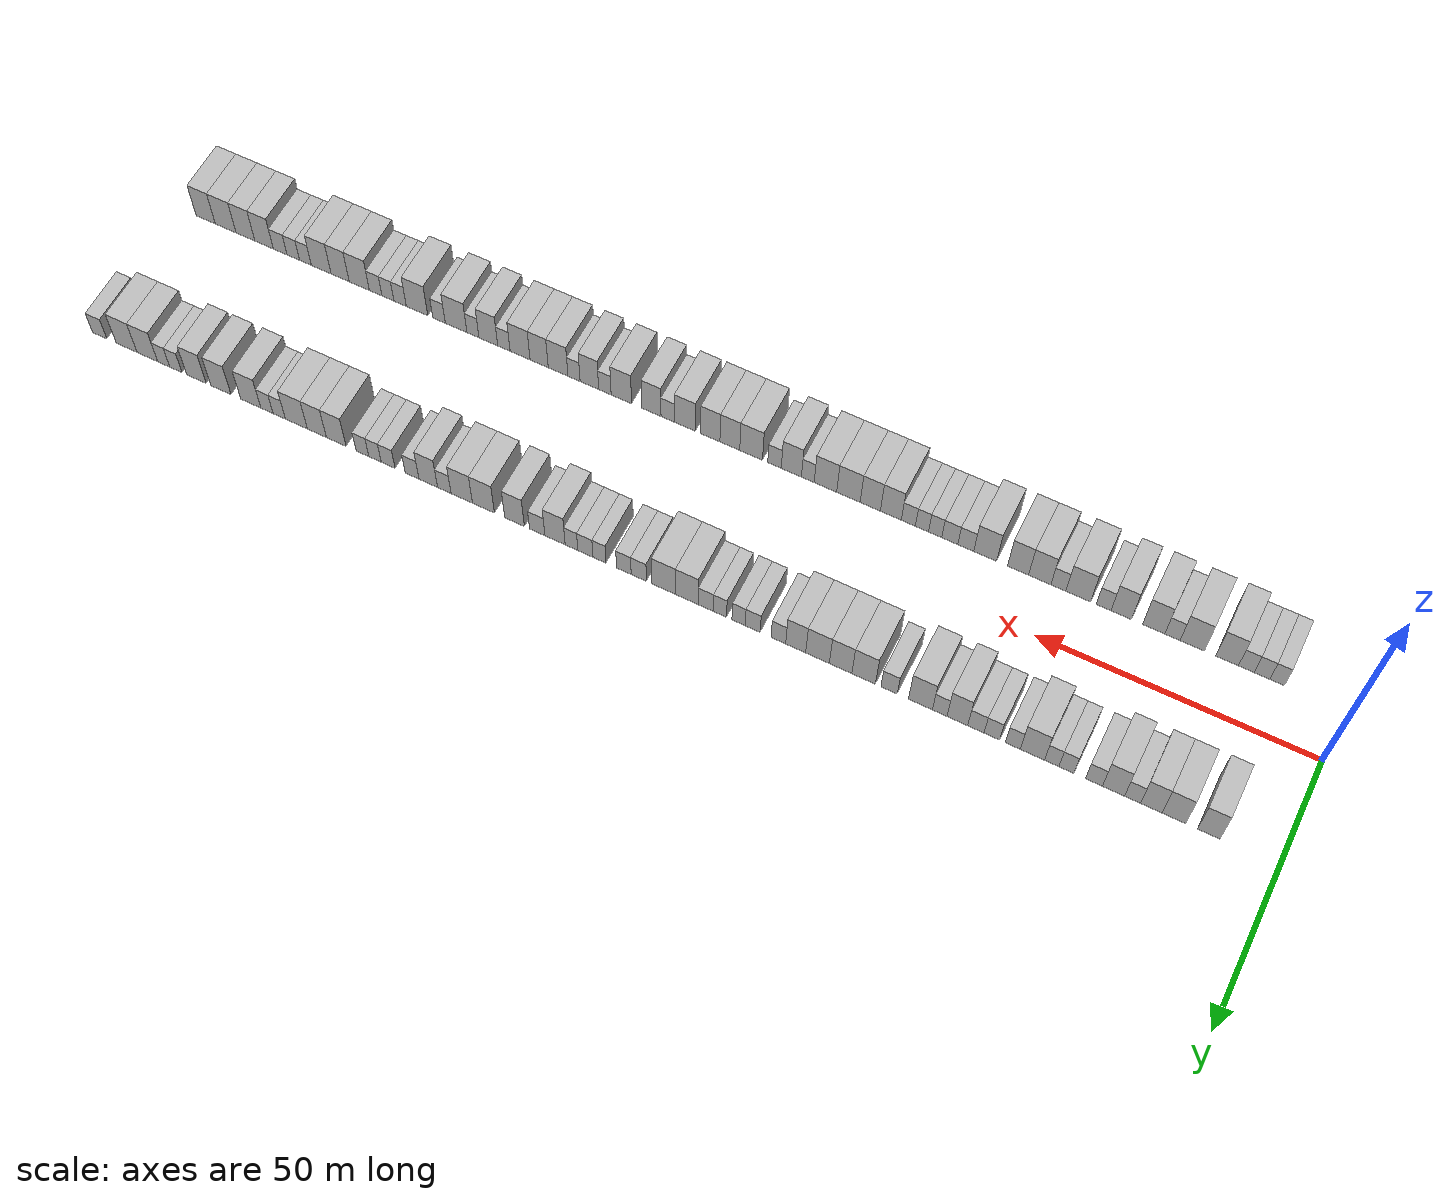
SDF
<sdf version="1.6">
 <world name="default">
  <scene>
   <sky><clouds><speed>12</speed></clouds></sky>
   <ambient>0.4 0.4 0.4 1</ambient>
   <background>0.7 0.7 0.7 1</background>
   <shadows>1</shadows>
  </scene>
  <gravity>0 0 -9.8066</gravity>
  <magnetic_field>6e-06 2.3e-05 -4.2e-05</magnetic_field>
  <physics default="0" name="default_physics" type="ode">
   <ode>
    <solver>
     <type>quick</type>
     <iters>10</iters>
     <sor>1.0</sor>
     <use_dynamic_moi_rescaling>0</use_dynamic_moi_rescaling>
    </solver>
    <constraints>
     <cfm>0</cfm>
     <erp>0.2</erp>
     <contact_max_correcting_vel>100</contact_max_correcting_vel>
     <contact_surface_layer>0.001</contact_surface_layer>
    </constraints>
   </ode>
   <max_step_size>0.004</max_step_size>
   <real_time_factor>1</real_time_factor>
   <real_time_update_rate>250</real_time_update_rate>
  </physics>
  <light name="sun" type="directional">
   <pose>0 0 10 0 0 0</pose>
   <diffuse>0.8 0.8 0.8 1</diffuse>
   <specular>0.2 0.2 0.2 1</specular>
   <attenuation>
    <range>1000</range>
    <constant>0.9</constant>
    <linear>0.01</linear>
    <quadratic>0.001</quadratic>
   </attenuation>
   <direction>-0.5 0.1 -0.9</direction>
  </light>
  <model name="building_1">
   <static>1</static>
   <pose>11.8929 15.0000 0 0.000000 0.000000 1.570796</pose>
   <link name="link">
    <pose>0 0 4.50 0 0 0</pose>
    <collision name="collision"><geometry><box><size>10.0000 3.7858 9.0000</size></box></geometry></collision>
    <visual name="visual">
     <cast_shadows>0</cast_shadows>
     <geometry><box><size>10.0000 3.7858 9.0000</size></box></geometry>
     <material>
      <script>
       <uri>model://HANNAS_wall/materials/scripts</uri>
       <uri>model://HANNAS_wall/materials/textures</uri>
       <name>vrc/HANNAS_wall</name>
      </script>
     </material>
    </visual>
   </link>
  </model>
  <model name="building_2">
   <static>1</static>
   <pose>17.8049 15.0000 0 0.000000 0.000000 1.570796</pose>
   <link name="link">
    <pose>0 0 4.50 0 0 0</pose>
    <collision name="collision"><geometry><box><size>10.0000 4.0382 9.0000</size></box></geometry></collision>
    <visual name="visual">
     <cast_shadows>0</cast_shadows>
     <geometry><box><size>10.0000 4.0382 9.0000</size></box></geometry>
     <material>
      <script>
       <uri>model://HANNAS_wall/materials/scripts</uri>
       <uri>model://HANNAS_wall/materials/textures</uri>
       <name>vrc/HANNAS_wall</name>
      </script>
     </material>
    </visual>
   </link>
  </model>
  <model name="building_3">
   <static>1</static>
   <pose>21.6515 15.0000 0 0.000000 0.000000 1.570796</pose>
   <link name="link">
    <pose>0 0 4.50 0 0 0</pose>
    <collision name="collision"><geometry><box><size>10.0000 3.6549 9.0000</size></box></geometry></collision>
    <visual name="visual">
     <cast_shadows>0</cast_shadows>
     <geometry><box><size>10.0000 3.6549 9.0000</size></box></geometry>
     <material>
      <script>
       <uri>model://HANNAS_wall/materials/scripts</uri>
       <uri>model://HANNAS_wall/materials/textures</uri>
       <name>vrc/HANNAS_wall</name>
      </script>
     </material>
    </visual>
   </link>
  </model>
  <model name="building_4">
   <static>1</static>
   <pose>24.8479 15.0000 0 0.000000 0.000000 1.570796</pose>
   <link name="link">
    <pose>0 0 3.00 0 0 0</pose>
    <collision name="collision"><geometry><box><size>10.0000 2.7379 6.0000</size></box></geometry></collision>
    <visual name="visual">
     <cast_shadows>0</cast_shadows>
     <geometry><box><size>10.0000 2.7379 6.0000</size></box></geometry>
     <material>
      <script>
       <uri>model://HANNAS_wall/materials/scripts</uri>
       <uri>model://HANNAS_wall/materials/textures</uri>
       <name>vrc/HANNAS_wall</name>
      </script>
     </material>
    </visual>
   </link>
  </model>
  <model name="building_5">
   <static>1</static>
   <pose>28.1217 15.0000 0 0.000000 0.000000 1.570796</pose>
   <link name="link">
    <pose>0 0 4.50 0 0 0</pose>
    <collision name="collision"><geometry><box><size>10.0000 3.8098 9.0000</size></box></geometry></collision>
    <visual name="visual">
     <cast_shadows>0</cast_shadows>
     <geometry><box><size>10.0000 3.8098 9.0000</size></box></geometry>
     <material>
      <script>
       <uri>model://HANNAS_wall/materials/scripts</uri>
       <uri>model://HANNAS_wall/materials/textures</uri>
       <name>vrc/HANNAS_wall</name>
      </script>
     </material>
    </visual>
   </link>
  </model>
  <model name="building_6">
   <static>1</static>
   <pose>31.4849 15.0000 0 0.000000 0.000000 1.570796</pose>
   <link name="link">
    <pose>0 0 3.00 0 0 0</pose>
    <collision name="collision"><geometry><box><size>10.0000 2.9166 6.0000</size></box></geometry></collision>
    <visual name="visual">
     <cast_shadows>0</cast_shadows>
     <geometry><box><size>10.0000 2.9166 6.0000</size></box></geometry>
     <material>
      <script>
       <uri>model://HANNAS_wall/materials/scripts</uri>
       <uri>model://HANNAS_wall/materials/textures</uri>
       <name>vrc/HANNAS_wall</name>
      </script>
     </material>
    </visual>
   </link>
  </model>
  <model name="building_7">
   <static>1</static>
   <pose>36.2474 15.0000 0 0.000000 0.000000 1.570796</pose>
   <link name="link">
    <pose>0 0 3.00 0 0 0</pose>
    <collision name="collision"><geometry><box><size>10.0000 2.6083 6.0000</size></box></geometry></collision>
    <visual name="visual">
     <cast_shadows>0</cast_shadows>
     <geometry><box><size>10.0000 2.6083 6.0000</size></box></geometry>
     <material>
      <script>
       <uri>model://HANNAS_wall/materials/scripts</uri>
       <uri>model://HANNAS_wall/materials/textures</uri>
       <name>vrc/HANNAS_wall</name>
      </script>
     </material>
    </visual>
   </link>
  </model>
  <model name="building_8">
   <static>1</static>
   <pose>38.7990 15.0000 0 0.000000 0.000000 1.570796</pose>
   <link name="link">
    <pose>0 0 3.00 0 0 0</pose>
    <collision name="collision"><geometry><box><size>10.0000 2.4950 6.0000</size></box></geometry></collision>
    <visual name="visual">
     <cast_shadows>0</cast_shadows>
     <geometry><box><size>10.0000 2.4950 6.0000</size></box></geometry>
     <material>
      <script>
       <uri>model://HANNAS_wall/materials/scripts</uri>
       <uri>model://HANNAS_wall/materials/textures</uri>
       <name>vrc/HANNAS_wall</name>
      </script>
     </material>
    </visual>
   </link>
  </model>
  <model name="building_9">
   <static>1</static>
   <pose>42.1642 15.0000 0 0.000000 0.000000 1.570796</pose>
   <link name="link">
    <pose>0 0 4.50 0 0 0</pose>
    <collision name="collision"><geometry><box><size>10.0000 4.2353 9.0000</size></box></geometry></collision>
    <visual name="visual">
     <cast_shadows>0</cast_shadows>
     <geometry><box><size>10.0000 4.2353 9.0000</size></box></geometry>
     <material>
      <script>
       <uri>model://HANNAS_wall/materials/scripts</uri>
       <uri>model://HANNAS_wall/materials/textures</uri>
       <name>vrc/HANNAS_wall</name>
      </script>
     </material>
    </visual>
   </link>
  </model>
  <model name="building_10">
   <static>1</static>
   <pose>45.5942 15.0000 0 0.000000 0.000000 1.570796</pose>
   <link name="link">
    <pose>0 0 3.00 0 0 0</pose>
    <collision name="collision"><geometry><box><size>10.0000 2.6246 6.0000</size></box></geometry></collision>
    <visual name="visual">
     <cast_shadows>0</cast_shadows>
     <geometry><box><size>10.0000 2.6246 6.0000</size></box></geometry>
     <material>
      <script>
       <uri>model://HANNAS_wall/materials/scripts</uri>
       <uri>model://HANNAS_wall/materials/textures</uri>
       <name>vrc/HANNAS_wall</name>
      </script>
     </material>
    </visual>
   </link>
  </model>
  <model name="building_11">
   <static>1</static>
   <pose>49.2856 15.0000 0 0.000000 0.000000 1.570796</pose>
   <link name="link">
    <pose>0 0 3.00 0 0 0</pose>
    <collision name="collision"><geometry><box><size>10.0000 2.7582 6.0000</size></box></geometry></collision>
    <visual name="visual">
     <cast_shadows>0</cast_shadows>
     <geometry><box><size>10.0000 2.7582 6.0000</size></box></geometry>
     <material>
      <script>
       <uri>model://HANNAS_wall/materials/scripts</uri>
       <uri>model://HANNAS_wall/materials/textures</uri>
       <name>vrc/HANNAS_wall</name>
      </script>
     </material>
    </visual>
   </link>
  </model>
  <model name="building_12">
   <static>1</static>
   <pose>52.1100 15.0000 0 0.000000 0.000000 1.570796</pose>
   <link name="link">
    <pose>0 0 3.00 0 0 0</pose>
    <collision name="collision"><geometry><box><size>10.0000 2.8906 6.0000</size></box></geometry></collision>
    <visual name="visual">
     <cast_shadows>0</cast_shadows>
     <geometry><box><size>10.0000 2.8906 6.0000</size></box></geometry>
     <material>
      <script>
       <uri>model://HANNAS_wall/materials/scripts</uri>
       <uri>model://HANNAS_wall/materials/textures</uri>
       <name>vrc/HANNAS_wall</name>
      </script>
     </material>
    </visual>
   </link>
  </model>
  <model name="building_13">
   <static>1</static>
   <pose>55.3930 15.0000 0 0.000000 0.000000 1.570796</pose>
   <link name="link">
    <pose>0 0 4.50 0 0 0</pose>
    <collision name="collision"><geometry><box><size>10.0000 3.6754 9.0000</size></box></geometry></collision>
    <visual name="visual">
     <cast_shadows>0</cast_shadows>
     <geometry><box><size>10.0000 3.6754 9.0000</size></box></geometry>
     <material>
      <script>
       <uri>model://HANNAS_wall/materials/scripts</uri>
       <uri>model://HANNAS_wall/materials/textures</uri>
       <name>vrc/HANNAS_wall</name>
      </script>
     </material>
    </visual>
   </link>
  </model>
  <model name="building_14">
   <static>1</static>
   <pose>58.5261 15.0000 0 0.000000 0.000000 1.570796</pose>
   <link name="link">
    <pose>0 0 3.00 0 0 0</pose>
    <collision name="collision"><geometry><box><size>10.0000 2.5907 6.0000</size></box></geometry></collision>
    <visual name="visual">
     <cast_shadows>0</cast_shadows>
     <geometry><box><size>10.0000 2.5907 6.0000</size></box></geometry>
     <material>
      <script>
       <uri>model://HANNAS_wall/materials/scripts</uri>
       <uri>model://HANNAS_wall/materials/textures</uri>
       <name>vrc/HANNAS_wall</name>
      </script>
     </material>
    </visual>
   </link>
  </model>
  <model name="building_15">
   <static>1</static>
   <pose>61.9586 15.0000 0 0.000000 0.000000 1.570796</pose>
   <link name="link">
    <pose>0 0 4.50 0 0 0</pose>
    <collision name="collision"><geometry><box><size>10.0000 4.2743 9.0000</size></box></geometry></collision>
    <visual name="visual">
     <cast_shadows>0</cast_shadows>
     <geometry><box><size>10.0000 4.2743 9.0000</size></box></geometry>
     <material>
      <script>
       <uri>model://HANNAS_wall/materials/scripts</uri>
       <uri>model://HANNAS_wall/materials/textures</uri>
       <name>vrc/HANNAS_wall</name>
      </script>
     </material>
    </visual>
   </link>
  </model>
  <model name="building_16">
   <static>1</static>
   <pose>67.5667 15.0000 0 0.000000 0.000000 1.570796</pose>
   <link name="link">
    <pose>0 0 3.00 0 0 0</pose>
    <collision name="collision"><geometry><box><size>10.0000 2.9419 6.0000</size></box></geometry></collision>
    <visual name="visual">
     <cast_shadows>0</cast_shadows>
     <geometry><box><size>10.0000 2.9419 6.0000</size></box></geometry>
     <material>
      <script>
       <uri>model://HANNAS_wall/materials/scripts</uri>
       <uri>model://HANNAS_wall/materials/textures</uri>
       <name>vrc/HANNAS_wall</name>
      </script>
     </material>
    </visual>
   </link>
  </model>
  <model name="building_17">
   <static>1</static>
   <pose>72.1605 15.0000 0 0.000000 0.000000 1.570796</pose>
   <link name="link">
    <pose>0 0 4.50 0 0 0</pose>
    <collision name="collision"><geometry><box><size>10.0000 4.2457 9.0000</size></box></geometry></collision>
    <visual name="visual">
     <cast_shadows>0</cast_shadows>
     <geometry><box><size>10.0000 4.2457 9.0000</size></box></geometry>
     <material>
      <script>
       <uri>model://HANNAS_wall/materials/scripts</uri>
       <uri>model://HANNAS_wall/materials/textures</uri>
       <name>vrc/HANNAS_wall</name>
      </script>
     </material>
    </visual>
   </link>
  </model>
  <model name="building_18">
   <static>1</static>
   <pose>76.3221 15.0000 0 0.000000 0.000000 1.570796</pose>
   <link name="link">
    <pose>0 0 4.50 0 0 0</pose>
    <collision name="collision"><geometry><box><size>10.0000 4.0774 9.0000</size></box></geometry></collision>
    <visual name="visual">
     <cast_shadows>0</cast_shadows>
     <geometry><box><size>10.0000 4.0774 9.0000</size></box></geometry>
     <material>
      <script>
       <uri>model://HANNAS_wall/materials/scripts</uri>
       <uri>model://HANNAS_wall/materials/textures</uri>
       <name>vrc/HANNAS_wall</name>
      </script>
     </material>
    </visual>
   </link>
  </model>
  <model name="building_19">
   <static>1</static>
   <pose>80.5234 15.0000 0 0.000000 0.000000 1.570796</pose>
   <link name="link">
    <pose>0 0 4.50 0 0 0</pose>
    <collision name="collision"><geometry><box><size>10.0000 4.3253 9.0000</size></box></geometry></collision>
    <visual name="visual">
     <cast_shadows>0</cast_shadows>
     <geometry><box><size>10.0000 4.3253 9.0000</size></box></geometry>
     <material>
      <script>
       <uri>model://HANNAS_wall/materials/scripts</uri>
       <uri>model://HANNAS_wall/materials/textures</uri>
       <name>vrc/HANNAS_wall</name>
      </script>
     </material>
    </visual>
   </link>
  </model>
  <model name="building_20">
   <static>1</static>
   <pose>84.5161 15.0000 0 0.000000 0.000000 1.570796</pose>
   <link name="link">
    <pose>0 0 4.50 0 0 0</pose>
    <collision name="collision"><geometry><box><size>10.0000 3.6600 9.0000</size></box></geometry></collision>
    <visual name="visual">
     <cast_shadows>0</cast_shadows>
     <geometry><box><size>10.0000 3.6600 9.0000</size></box></geometry>
     <material>
      <script>
       <uri>model://HANNAS_wall/materials/scripts</uri>
       <uri>model://HANNAS_wall/materials/textures</uri>
       <name>vrc/HANNAS_wall</name>
      </script>
     </material>
    </visual>
   </link>
  </model>
  <model name="building_21">
   <static>1</static>
   <pose>87.6903 15.0000 0 0.000000 0.000000 1.570796</pose>
   <link name="link">
    <pose>0 0 3.00 0 0 0</pose>
    <collision name="collision"><geometry><box><size>10.0000 2.6885 6.0000</size></box></geometry></collision>
    <visual name="visual">
     <cast_shadows>0</cast_shadows>
     <geometry><box><size>10.0000 2.6885 6.0000</size></box></geometry>
     <material>
      <script>
       <uri>model://HANNAS_wall/materials/scripts</uri>
       <uri>model://HANNAS_wall/materials/textures</uri>
       <name>vrc/HANNAS_wall</name>
      </script>
     </material>
    </visual>
   </link>
  </model>
  <model name="building_22">
   <static>1</static>
   <pose>92.4171 15.0000 0 0.000000 0.000000 1.570796</pose>
   <link name="link">
    <pose>0 0 3.00 0 0 0</pose>
    <collision name="collision"><geometry><box><size>10.0000 2.7649 6.0000</size></box></geometry></collision>
    <visual name="visual">
     <cast_shadows>0</cast_shadows>
     <geometry><box><size>10.0000 2.7649 6.0000</size></box></geometry>
     <material>
      <script>
       <uri>model://HANNAS_wall/materials/scripts</uri>
       <uri>model://HANNAS_wall/materials/textures</uri>
       <name>vrc/HANNAS_wall</name>
      </script>
     </material>
    </visual>
   </link>
  </model>
  <model name="building_23">
   <static>1</static>
   <pose>95.0302 15.0000 0 0.000000 0.000000 1.570796</pose>
   <link name="link">
    <pose>0 0 3.00 0 0 0</pose>
    <collision name="collision"><geometry><box><size>10.0000 2.4614 6.0000</size></box></geometry></collision>
    <visual name="visual">
     <cast_shadows>0</cast_shadows>
     <geometry><box><size>10.0000 2.4614 6.0000</size></box></geometry>
     <material>
      <script>
       <uri>model://HANNAS_wall/materials/scripts</uri>
       <uri>model://HANNAS_wall/materials/textures</uri>
       <name>vrc/HANNAS_wall</name>
      </script>
     </material>
    </visual>
   </link>
  </model>
  <model name="building_24">
   <static>1</static>
   <pose>98.5067 15.0000 0 0.000000 0.000000 1.570796</pose>
   <link name="link">
    <pose>0 0 3.00 0 0 0</pose>
    <collision name="collision"><geometry><box><size>10.0000 2.4915 6.0000</size></box></geometry></collision>
    <visual name="visual">
     <cast_shadows>0</cast_shadows>
     <geometry><box><size>10.0000 2.4915 6.0000</size></box></geometry>
     <material>
      <script>
       <uri>model://HANNAS_wall/materials/scripts</uri>
       <uri>model://HANNAS_wall/materials/textures</uri>
       <name>vrc/HANNAS_wall</name>
      </script>
     </material>
    </visual>
   </link>
  </model>
  <model name="building_25">
   <static>1</static>
   <pose>101.1531 15.0000 0 0.000000 0.000000 1.570796</pose>
   <link name="link">
    <pose>0 0 3.00 0 0 0</pose>
    <collision name="collision"><geometry><box><size>10.0000 2.8013 6.0000</size></box></geometry></collision>
    <visual name="visual">
     <cast_shadows>0</cast_shadows>
     <geometry><box><size>10.0000 2.8013 6.0000</size></box></geometry>
     <material>
      <script>
       <uri>model://HANNAS_wall/materials/scripts</uri>
       <uri>model://HANNAS_wall/materials/textures</uri>
       <name>vrc/HANNAS_wall</name>
      </script>
     </material>
    </visual>
   </link>
  </model>
  <model name="building_26">
   <static>1</static>
   <pose>104.6745 15.0000 0 0.000000 0.000000 1.570796</pose>
   <link name="link">
    <pose>0 0 4.50 0 0 0</pose>
    <collision name="collision"><geometry><box><size>10.0000 4.2414 9.0000</size></box></geometry></collision>
    <visual name="visual">
     <cast_shadows>0</cast_shadows>
     <geometry><box><size>10.0000 4.2414 9.0000</size></box></geometry>
     <material>
      <script>
       <uri>model://HANNAS_wall/materials/scripts</uri>
       <uri>model://HANNAS_wall/materials/textures</uri>
       <name>vrc/HANNAS_wall</name>
      </script>
     </material>
    </visual>
   </link>
  </model>
  <model name="building_27">
   <static>1</static>
   <pose>109.0264 15.0000 0 0.000000 0.000000 1.570796</pose>
   <link name="link">
    <pose>0 0 4.50 0 0 0</pose>
    <collision name="collision"><geometry><box><size>10.0000 4.4623 9.0000</size></box></geometry></collision>
    <visual name="visual">
     <cast_shadows>0</cast_shadows>
     <geometry><box><size>10.0000 4.4623 9.0000</size></box></geometry>
     <material>
      <script>
       <uri>model://HANNAS_wall/materials/scripts</uri>
       <uri>model://HANNAS_wall/materials/textures</uri>
       <name>vrc/HANNAS_wall</name>
      </script>
     </material>
    </visual>
   </link>
  </model>
  <model name="building_28">
   <static>1</static>
   <pose>113.6944 15.0000 0 0.000000 0.000000 1.570796</pose>
   <link name="link">
    <pose>0 0 3.00 0 0 0</pose>
    <collision name="collision"><geometry><box><size>10.0000 2.8739 6.0000</size></box></geometry></collision>
    <visual name="visual">
     <cast_shadows>0</cast_shadows>
     <geometry><box><size>10.0000 2.8739 6.0000</size></box></geometry>
     <material>
      <script>
       <uri>model://HANNAS_wall/materials/scripts</uri>
       <uri>model://HANNAS_wall/materials/textures</uri>
       <name>vrc/HANNAS_wall</name>
      </script>
     </material>
    </visual>
   </link>
  </model>
  <model name="building_29">
   <static>1</static>
   <pose>116.5172 15.0000 0 0.000000 0.000000 1.570796</pose>
   <link name="link">
    <pose>0 0 3.00 0 0 0</pose>
    <collision name="collision"><geometry><box><size>10.0000 2.7716 6.0000</size></box></geometry></collision>
    <visual name="visual">
     <cast_shadows>0</cast_shadows>
     <geometry><box><size>10.0000 2.7716 6.0000</size></box></geometry>
     <material>
      <script>
       <uri>model://HANNAS_wall/materials/scripts</uri>
       <uri>model://HANNAS_wall/materials/textures</uri>
       <name>vrc/HANNAS_wall</name>
      </script>
     </material>
    </visual>
   </link>
  </model>
  <model name="building_30">
   <static>1</static>
   <pose>121.1402 15.0000 0 0.000000 0.000000 1.570796</pose>
   <link name="link">
    <pose>0 0 3.00 0 0 0</pose>
    <collision name="collision"><geometry><box><size>10.0000 2.4743 6.0000</size></box></geometry></collision>
    <visual name="visual">
     <cast_shadows>0</cast_shadows>
     <geometry><box><size>10.0000 2.4743 6.0000</size></box></geometry>
     <material>
      <script>
       <uri>model://HANNAS_wall/materials/scripts</uri>
       <uri>model://HANNAS_wall/materials/textures</uri>
       <name>vrc/HANNAS_wall</name>
      </script>
     </material>
    </visual>
   </link>
  </model>
  <model name="building_31">
   <static>1</static>
   <pose>123.8260 15.0000 0 0.000000 0.000000 1.570796</pose>
   <link name="link">
    <pose>0 0 3.00 0 0 0</pose>
    <collision name="collision"><geometry><box><size>10.0000 2.8974 6.0000</size></box></geometry></collision>
    <visual name="visual">
     <cast_shadows>0</cast_shadows>
     <geometry><box><size>10.0000 2.8974 6.0000</size></box></geometry>
     <material>
      <script>
       <uri>model://HANNAS_wall/materials/scripts</uri>
       <uri>model://HANNAS_wall/materials/textures</uri>
       <name>vrc/HANNAS_wall</name>
      </script>
     </material>
    </visual>
   </link>
  </model>
  <model name="building_32">
   <static>1</static>
   <pose>126.4903 15.0000 0 0.000000 0.000000 1.570796</pose>
   <link name="link">
    <pose>0 0 3.00 0 0 0</pose>
    <collision name="collision"><geometry><box><size>10.0000 2.4313 6.0000</size></box></geometry></collision>
    <visual name="visual">
     <cast_shadows>0</cast_shadows>
     <geometry><box><size>10.0000 2.4313 6.0000</size></box></geometry>
     <material>
      <script>
       <uri>model://HANNAS_wall/materials/scripts</uri>
       <uri>model://HANNAS_wall/materials/textures</uri>
       <name>vrc/HANNAS_wall</name>
      </script>
     </material>
    </visual>
   </link>
  </model>
  <model name="building_33">
   <static>1</static>
   <pose>129.6501 15.0000 0 0.000000 0.000000 1.570796</pose>
   <link name="link">
    <pose>0 0 4.50 0 0 0</pose>
    <collision name="collision"><geometry><box><size>10.0000 3.8882 9.0000</size></box></geometry></collision>
    <visual name="visual">
     <cast_shadows>0</cast_shadows>
     <geometry><box><size>10.0000 3.8882 9.0000</size></box></geometry>
     <material>
      <script>
       <uri>model://HANNAS_wall/materials/scripts</uri>
       <uri>model://HANNAS_wall/materials/textures</uri>
       <name>vrc/HANNAS_wall</name>
      </script>
     </material>
    </visual>
   </link>
  </model>
  <model name="building_34">
   <static>1</static>
   <pose>133.0760 15.0000 0 0.000000 0.000000 1.570796</pose>
   <link name="link">
    <pose>0 0 3.00 0 0 0</pose>
    <collision name="collision"><geometry><box><size>10.0000 2.9636 6.0000</size></box></geometry></collision>
    <visual name="visual">
     <cast_shadows>0</cast_shadows>
     <geometry><box><size>10.0000 2.9636 6.0000</size></box></geometry>
     <material>
      <script>
       <uri>model://HANNAS_wall/materials/scripts</uri>
       <uri>model://HANNAS_wall/materials/textures</uri>
       <name>vrc/HANNAS_wall</name>
      </script>
     </material>
    </visual>
   </link>
  </model>
  <model name="building_35">
   <static>1</static>
   <pose>137.4573 15.0000 0 0.000000 0.000000 1.570796</pose>
   <link name="link">
    <pose>0 0 4.50 0 0 0</pose>
    <collision name="collision"><geometry><box><size>10.0000 3.7990 9.0000</size></box></geometry></collision>
    <visual name="visual">
     <cast_shadows>0</cast_shadows>
     <geometry><box><size>10.0000 3.7990 9.0000</size></box></geometry>
     <material>
      <script>
       <uri>model://HANNAS_wall/materials/scripts</uri>
       <uri>model://HANNAS_wall/materials/textures</uri>
       <name>vrc/HANNAS_wall</name>
      </script>
     </material>
    </visual>
   </link>
  </model>
  <model name="building_36">
   <static>1</static>
   <pose>143.5039 15.0000 0 0.000000 0.000000 1.570796</pose>
   <link name="link">
    <pose>0 0 4.50 0 0 0</pose>
    <collision name="collision"><geometry><box><size>10.0000 4.2943 9.0000</size></box></geometry></collision>
    <visual name="visual">
     <cast_shadows>0</cast_shadows>
     <geometry><box><size>10.0000 4.2943 9.0000</size></box></geometry>
     <material>
      <script>
       <uri>model://HANNAS_wall/materials/scripts</uri>
       <uri>model://HANNAS_wall/materials/textures</uri>
       <name>vrc/HANNAS_wall</name>
      </script>
     </material>
    </visual>
   </link>
  </model>
  <model name="building_37">
   <static>1</static>
   <pose>147.7467 15.0000 0 0.000000 0.000000 1.570796</pose>
   <link name="link">
    <pose>0 0 4.50 0 0 0</pose>
    <collision name="collision"><geometry><box><size>10.0000 4.1912 9.0000</size></box></geometry></collision>
    <visual name="visual">
     <cast_shadows>0</cast_shadows>
     <geometry><box><size>10.0000 4.1912 9.0000</size></box></geometry>
     <material>
      <script>
       <uri>model://HANNAS_wall/materials/scripts</uri>
       <uri>model://HANNAS_wall/materials/textures</uri>
       <name>vrc/HANNAS_wall</name>
      </script>
     </material>
    </visual>
   </link>
  </model>
  <model name="building_38">
   <static>1</static>
   <pose>151.1695 15.0000 0 0.000000 0.000000 1.570796</pose>
   <link name="link">
    <pose>0 0 3.00 0 0 0</pose>
    <collision name="collision"><geometry><box><size>10.0000 2.6546 6.0000</size></box></geometry></collision>
    <visual name="visual">
     <cast_shadows>0</cast_shadows>
     <geometry><box><size>10.0000 2.6546 6.0000</size></box></geometry>
     <material>
      <script>
       <uri>model://HANNAS_wall/materials/scripts</uri>
       <uri>model://HANNAS_wall/materials/textures</uri>
       <name>vrc/HANNAS_wall</name>
      </script>
     </material>
    </visual>
   </link>
  </model>
  <model name="building_39">
   <static>1</static>
   <pose>154.3343 15.0000 0 0.000000 0.000000 1.570796</pose>
   <link name="link">
    <pose>0 0 4.50 0 0 0</pose>
    <collision name="collision"><geometry><box><size>10.0000 3.6749 9.0000</size></box></geometry></collision>
    <visual name="visual">
     <cast_shadows>0</cast_shadows>
     <geometry><box><size>10.0000 3.6749 9.0000</size></box></geometry>
     <material>
      <script>
       <uri>model://HANNAS_wall/materials/scripts</uri>
       <uri>model://HANNAS_wall/materials/textures</uri>
       <name>vrc/HANNAS_wall</name>
      </script>
     </material>
    </visual>
   </link>
  </model>
  <model name="building_40">
   <static>1</static>
   <pose>157.5388 15.0000 0 0.000000 0.000000 1.570796</pose>
   <link name="link">
    <pose>0 0 3.00 0 0 0</pose>
    <collision name="collision"><geometry><box><size>10.0000 2.7341 6.0000</size></box></geometry></collision>
    <visual name="visual">
     <cast_shadows>0</cast_shadows>
     <geometry><box><size>10.0000 2.7341 6.0000</size></box></geometry>
     <material>
      <script>
       <uri>model://HANNAS_wall/materials/scripts</uri>
       <uri>model://HANNAS_wall/materials/textures</uri>
       <name>vrc/HANNAS_wall</name>
      </script>
     </material>
    </visual>
   </link>
  </model>
  <model name="building_41">
   <static>1</static>
   <pose>162.2911 15.0000 0 0.000000 0.000000 1.570796</pose>
   <link name="link">
    <pose>0 0 3.00 0 0 0</pose>
    <collision name="collision"><geometry><box><size>10.0000 2.7706 6.0000</size></box></geometry></collision>
    <visual name="visual">
     <cast_shadows>0</cast_shadows>
     <geometry><box><size>10.0000 2.7706 6.0000</size></box></geometry>
     <material>
      <script>
       <uri>model://HANNAS_wall/materials/scripts</uri>
       <uri>model://HANNAS_wall/materials/textures</uri>
       <name>vrc/HANNAS_wall</name>
      </script>
     </material>
    </visual>
   </link>
  </model>
  <model name="building_42">
   <static>1</static>
   <pose>164.9075 15.0000 0 0.000000 0.000000 1.570796</pose>
   <link name="link">
    <pose>0 0 3.00 0 0 0</pose>
    <collision name="collision"><geometry><box><size>10.0000 2.4622 6.0000</size></box></geometry></collision>
    <visual name="visual">
     <cast_shadows>0</cast_shadows>
     <geometry><box><size>10.0000 2.4622 6.0000</size></box></geometry>
     <material>
      <script>
       <uri>model://HANNAS_wall/materials/scripts</uri>
       <uri>model://HANNAS_wall/materials/textures</uri>
       <name>vrc/HANNAS_wall</name>
      </script>
     </material>
    </visual>
   </link>
  </model>
  <model name="building_43">
   <static>1</static>
   <pose>167.4110 15.0000 0 0.000000 0.000000 1.570796</pose>
   <link name="link">
    <pose>0 0 3.00 0 0 0</pose>
    <collision name="collision"><geometry><box><size>10.0000 2.5448 6.0000</size></box></geometry></collision>
    <visual name="visual">
     <cast_shadows>0</cast_shadows>
     <geometry><box><size>10.0000 2.5448 6.0000</size></box></geometry>
     <material>
      <script>
       <uri>model://HANNAS_wall/materials/scripts</uri>
       <uri>model://HANNAS_wall/materials/textures</uri>
       <name>vrc/HANNAS_wall</name>
      </script>
     </material>
    </visual>
   </link>
  </model>
  <model name="building_44">
   <static>1</static>
   <pose>172.6693 15.0000 0 0.000000 0.000000 1.570796</pose>
   <link name="link">
    <pose>0 0 4.50 0 0 0</pose>
    <collision name="collision"><geometry><box><size>10.0000 3.9719 9.0000</size></box></geometry></collision>
    <visual name="visual">
     <cast_shadows>0</cast_shadows>
     <geometry><box><size>10.0000 3.9719 9.0000</size></box></geometry>
     <material>
      <script>
       <uri>model://HANNAS_wall/materials/scripts</uri>
       <uri>model://HANNAS_wall/materials/textures</uri>
       <name>vrc/HANNAS_wall</name>
      </script>
     </material>
    </visual>
   </link>
  </model>
  <model name="building_45">
   <static>1</static>
   <pose>176.5831 15.0000 0 0.000000 0.000000 1.570796</pose>
   <link name="link">
    <pose>0 0 4.50 0 0 0</pose>
    <collision name="collision"><geometry><box><size>10.0000 3.8555 9.0000</size></box></geometry></collision>
    <visual name="visual">
     <cast_shadows>0</cast_shadows>
     <geometry><box><size>10.0000 3.8555 9.0000</size></box></geometry>
     <material>
      <script>
       <uri>model://HANNAS_wall/materials/scripts</uri>
       <uri>model://HANNAS_wall/materials/textures</uri>
       <name>vrc/HANNAS_wall</name>
      </script>
     </material>
    </visual>
   </link>
  </model>
  <model name="building_46">
   <static>1</static>
   <pose>180.7405 15.0000 0 0.000000 0.000000 1.570796</pose>
   <link name="link">
    <pose>0 0 4.50 0 0 0</pose>
    <collision name="collision"><geometry><box><size>10.0000 4.4594 9.0000</size></box></geometry></collision>
    <visual name="visual">
     <cast_shadows>0</cast_shadows>
     <geometry><box><size>10.0000 4.4594 9.0000</size></box></geometry>
     <material>
      <script>
       <uri>model://HANNAS_wall/materials/scripts</uri>
       <uri>model://HANNAS_wall/materials/textures</uri>
       <name>vrc/HANNAS_wall</name>
      </script>
     </material>
    </visual>
   </link>
  </model>
  <model name="building_47">
   <static>1</static>
   <pose>184.2190 15.0000 0 0.000000 0.000000 1.570796</pose>
   <link name="link">
    <pose>0 0 3.00 0 0 0</pose>
    <collision name="collision"><geometry><box><size>10.0000 2.4976 6.0000</size></box></geometry></collision>
    <visual name="visual">
     <cast_shadows>0</cast_shadows>
     <geometry><box><size>10.0000 2.4976 6.0000</size></box></geometry>
     <material>
      <script>
       <uri>model://HANNAS_wall/materials/scripts</uri>
       <uri>model://HANNAS_wall/materials/textures</uri>
       <name>vrc/HANNAS_wall</name>
      </script>
     </material>
    </visual>
   </link>
  </model>
  <model name="building_48">
   <static>1</static>
   <pose>186.7154 15.0000 0 0.000000 0.000000 1.570796</pose>
   <link name="link">
    <pose>0 0 3.00 0 0 0</pose>
    <collision name="collision"><geometry><box><size>10.0000 2.4953 6.0000</size></box></geometry></collision>
    <visual name="visual">
     <cast_shadows>0</cast_shadows>
     <geometry><box><size>10.0000 2.4953 6.0000</size></box></geometry>
     <material>
      <script>
       <uri>model://HANNAS_wall/materials/scripts</uri>
       <uri>model://HANNAS_wall/materials/textures</uri>
       <name>vrc/HANNAS_wall</name>
      </script>
     </material>
    </visual>
   </link>
  </model>
  <model name="building_49">
   <static>1</static>
   <pose>190.0253 15.0000 0 0.000000 0.000000 1.570796</pose>
   <link name="link">
    <pose>0 0 4.50 0 0 0</pose>
    <collision name="collision"><geometry><box><size>10.0000 4.1245 9.0000</size></box></geometry></collision>
    <visual name="visual">
     <cast_shadows>0</cast_shadows>
     <geometry><box><size>10.0000 4.1245 9.0000</size></box></geometry>
     <material>
      <script>
       <uri>model://HANNAS_wall/materials/scripts</uri>
       <uri>model://HANNAS_wall/materials/textures</uri>
       <name>vrc/HANNAS_wall</name>
      </script>
     </material>
    </visual>
   </link>
  </model>
  <model name="building_50">
   <static>1</static>
   <pose>196.1464 15.0000 0 0.000000 0.000000 1.570796</pose>
   <link name="link">
    <pose>0 0 4.50 0 0 0</pose>
    <collision name="collision"><geometry><box><size>10.0000 4.1176 9.0000</size></box></geometry></collision>
    <visual name="visual">
     <cast_shadows>0</cast_shadows>
     <geometry><box><size>10.0000 4.1176 9.0000</size></box></geometry>
     <material>
      <script>
       <uri>model://HANNAS_wall/materials/scripts</uri>
       <uri>model://HANNAS_wall/materials/textures</uri>
       <name>vrc/HANNAS_wall</name>
      </script>
     </material>
    </visual>
   </link>
  </model>
  <model name="building_51">
   <static>1</static>
   <pose>201.2211 15.0000 0 0.000000 0.000000 1.570796</pose>
   <link name="link">
    <pose>0 0 4.50 0 0 0</pose>
    <collision name="collision"><geometry><box><size>10.0000 4.0319 9.0000</size></box></geometry></collision>
    <visual name="visual">
     <cast_shadows>0</cast_shadows>
     <geometry><box><size>10.0000 4.0319 9.0000</size></box></geometry>
     <material>
      <script>
       <uri>model://HANNAS_wall/materials/scripts</uri>
       <uri>model://HANNAS_wall/materials/textures</uri>
       <name>vrc/HANNAS_wall</name>
      </script>
     </material>
    </visual>
   </link>
  </model>
  <model name="building_52">
   <static>1</static>
   <pose>205.5053 15.0000 0 0.000000 0.000000 1.570796</pose>
   <link name="link">
    <pose>0 0 3.00 0 0 0</pose>
    <collision name="collision"><geometry><box><size>10.0000 2.5364 6.0000</size></box></geometry></collision>
    <visual name="visual">
     <cast_shadows>0</cast_shadows>
     <geometry><box><size>10.0000 2.5364 6.0000</size></box></geometry>
     <material>
      <script>
       <uri>model://HANNAS_wall/materials/scripts</uri>
       <uri>model://HANNAS_wall/materials/textures</uri>
       <name>vrc/HANNAS_wall</name>
      </script>
     </material>
    </visual>
   </link>
  </model>
  <model name="building_53">
   <static>1</static>
   <pose>208.0329 15.0000 0 0.000000 0.000000 1.570796</pose>
   <link name="link">
    <pose>0 0 3.00 0 0 0</pose>
    <collision name="collision"><geometry><box><size>10.0000 2.5187 6.0000</size></box></geometry></collision>
    <visual name="visual">
     <cast_shadows>0</cast_shadows>
     <geometry><box><size>10.0000 2.5187 6.0000</size></box></geometry>
     <material>
      <script>
       <uri>model://HANNAS_wall/materials/scripts</uri>
       <uri>model://HANNAS_wall/materials/textures</uri>
       <name>vrc/HANNAS_wall</name>
      </script>
     </material>
    </visual>
   </link>
  </model>
  <model name="building_54">
   <static>1</static>
   <pose>211.4570 15.0000 0 0.000000 0.000000 1.570796</pose>
   <link name="link">
    <pose>0 0 4.50 0 0 0</pose>
    <collision name="collision"><geometry><box><size>10.0000 4.3296 9.0000</size></box></geometry></collision>
    <visual name="visual">
     <cast_shadows>0</cast_shadows>
     <geometry><box><size>10.0000 4.3296 9.0000</size></box></geometry>
     <material>
      <script>
       <uri>model://HANNAS_wall/materials/scripts</uri>
       <uri>model://HANNAS_wall/materials/textures</uri>
       <name>vrc/HANNAS_wall</name>
      </script>
     </material>
    </visual>
   </link>
  </model>
  <model name="building_55">
   <static>1</static>
   <pose>215.8085 15.0000 0 0.000000 0.000000 1.570796</pose>
   <link name="link">
    <pose>0 0 4.50 0 0 0</pose>
    <collision name="collision"><geometry><box><size>10.0000 4.3734 9.0000</size></box></geometry></collision>
    <visual name="visual">
     <cast_shadows>0</cast_shadows>
     <geometry><box><size>10.0000 4.3734 9.0000</size></box></geometry>
     <material>
      <script>
       <uri>model://HANNAS_wall/materials/scripts</uri>
       <uri>model://HANNAS_wall/materials/textures</uri>
       <name>vrc/HANNAS_wall</name>
      </script>
     </material>
    </visual>
   </link>
  </model>
  <model name="building_56">
   <static>1</static>
   <pose>221.4932 15.0000 0 0.000000 0.000000 1.570796</pose>
   <link name="link">
    <pose>0 0 3.00 0 0 0</pose>
    <collision name="collision"><geometry><box><size>10.0000 2.9960 6.0000</size></box></geometry></collision>
    <visual name="visual">
     <cast_shadows>0</cast_shadows>
     <geometry><box><size>10.0000 2.9960 6.0000</size></box></geometry>
     <material>
      <script>
       <uri>model://HANNAS_wall/materials/scripts</uri>
       <uri>model://HANNAS_wall/materials/textures</uri>
       <name>vrc/HANNAS_wall</name>
      </script>
     </material>
    </visual>
   </link>
  </model>
  <model name="building_57">
   <static>1</static>
   <pose>11.2732 -15.0000 0 0.000000 0.000000 1.570796</pose>
   <link name="link">
    <pose>0 0 3.00 0 0 0</pose>
    <collision name="collision"><geometry><box><size>10.0000 2.5463 6.0000</size></box></geometry></collision>
    <visual name="visual">
     <cast_shadows>0</cast_shadows>
     <geometry><box><size>10.0000 2.5463 6.0000</size></box></geometry>
     <material>
      <script>
       <uri>model://HANNAS_wall/materials/scripts</uri>
       <uri>model://HANNAS_wall/materials/textures</uri>
       <name>vrc/HANNAS_wall</name>
      </script>
     </material>
    </visual>
   </link>
  </model>
  <model name="building_58">
   <static>1</static>
   <pose>13.8984 -15.0000 0 0.000000 0.000000 1.570796</pose>
   <link name="link">
    <pose>0 0 3.00 0 0 0</pose>
    <collision name="collision"><geometry><box><size>10.0000 2.7041 6.0000</size></box></geometry></collision>
    <visual name="visual">
     <cast_shadows>0</cast_shadows>
     <geometry><box><size>10.0000 2.7041 6.0000</size></box></geometry>
     <material>
      <script>
       <uri>model://HANNAS_wall/materials/scripts</uri>
       <uri>model://HANNAS_wall/materials/textures</uri>
       <name>vrc/HANNAS_wall</name>
      </script>
     </material>
    </visual>
   </link>
  </model>
  <model name="building_59">
   <static>1</static>
   <pose>16.6258 -15.0000 0 0.000000 0.000000 1.570796</pose>
   <link name="link">
    <pose>0 0 3.00 0 0 0</pose>
    <collision name="collision"><geometry><box><size>10.0000 2.7507 6.0000</size></box></geometry></collision>
    <visual name="visual">
     <cast_shadows>0</cast_shadows>
     <geometry><box><size>10.0000 2.7507 6.0000</size></box></geometry>
     <material>
      <script>
       <uri>model://HANNAS_wall/materials/scripts</uri>
       <uri>model://HANNAS_wall/materials/textures</uri>
       <name>vrc/HANNAS_wall</name>
      </script>
     </material>
    </visual>
   </link>
  </model>
  <model name="building_60">
   <static>1</static>
   <pose>19.9818 -15.0000 0 0.000000 0.000000 1.570796</pose>
   <link name="link">
    <pose>0 0 4.50 0 0 0</pose>
    <collision name="collision"><geometry><box><size>10.0000 3.9614 9.0000</size></box></geometry></collision>
    <visual name="visual">
     <cast_shadows>0</cast_shadows>
     <geometry><box><size>10.0000 3.9614 9.0000</size></box></geometry>
     <material>
      <script>
       <uri>model://HANNAS_wall/materials/scripts</uri>
       <uri>model://HANNAS_wall/materials/textures</uri>
       <name>vrc/HANNAS_wall</name>
      </script>
     </material>
    </visual>
   </link>
  </model>
  <model name="building_61">
   <static>1</static>
   <pose>26.1004 -15.0000 0 0.000000 0.000000 1.570796</pose>
   <link name="link">
    <pose>0 0 4.50 0 0 0</pose>
    <collision name="collision"><geometry><box><size>10.0000 4.2758 9.0000</size></box></geometry></collision>
    <visual name="visual">
     <cast_shadows>0</cast_shadows>
     <geometry><box><size>10.0000 4.2758 9.0000</size></box></geometry>
     <material>
      <script>
       <uri>model://HANNAS_wall/materials/scripts</uri>
       <uri>model://HANNAS_wall/materials/textures</uri>
       <name>vrc/HANNAS_wall</name>
      </script>
     </material>
    </visual>
   </link>
  </model>
  <model name="building_62">
   <static>1</static>
   <pose>29.5896 -15.0000 0 0.000000 0.000000 1.570796</pose>
   <link name="link">
    <pose>0 0 3.00 0 0 0</pose>
    <collision name="collision"><geometry><box><size>10.0000 2.7027 6.0000</size></box></geometry></collision>
    <visual name="visual">
     <cast_shadows>0</cast_shadows>
     <geometry><box><size>10.0000 2.7027 6.0000</size></box></geometry>
     <material>
      <script>
       <uri>model://HANNAS_wall/materials/scripts</uri>
       <uri>model://HANNAS_wall/materials/textures</uri>
       <name>vrc/HANNAS_wall</name>
      </script>
     </material>
    </visual>
   </link>
  </model>
  <model name="building_63">
   <static>1</static>
   <pose>32.9135 -15.0000 0 0.000000 0.000000 1.570796</pose>
   <link name="link">
    <pose>0 0 4.50 0 0 0</pose>
    <collision name="collision"><geometry><box><size>10.0000 3.9450 9.0000</size></box></geometry></collision>
    <visual name="visual">
     <cast_shadows>0</cast_shadows>
     <geometry><box><size>10.0000 3.9450 9.0000</size></box></geometry>
     <material>
      <script>
       <uri>model://HANNAS_wall/materials/scripts</uri>
       <uri>model://HANNAS_wall/materials/textures</uri>
       <name>vrc/HANNAS_wall</name>
      </script>
     </material>
    </visual>
   </link>
  </model>
  <model name="building_64">
   <static>1</static>
   <pose>38.7111 -15.0000 0 0.000000 0.000000 1.570796</pose>
   <link name="link">
    <pose>0 0 4.50 0 0 0</pose>
    <collision name="collision"><geometry><box><size>10.0000 3.6503 9.0000</size></box></geometry></collision>
    <visual name="visual">
     <cast_shadows>0</cast_shadows>
     <geometry><box><size>10.0000 3.6503 9.0000</size></box></geometry>
     <material>
      <script>
       <uri>model://HANNAS_wall/materials/scripts</uri>
       <uri>model://HANNAS_wall/materials/textures</uri>
       <name>vrc/HANNAS_wall</name>
      </script>
     </material>
    </visual>
   </link>
  </model>
  <model name="building_65">
   <static>1</static>
   <pose>41.8596 -15.0000 0 0.000000 0.000000 1.570796</pose>
   <link name="link">
    <pose>0 0 3.00 0 0 0</pose>
    <collision name="collision"><geometry><box><size>10.0000 2.6468 6.0000</size></box></geometry></collision>
    <visual name="visual">
     <cast_shadows>0</cast_shadows>
     <geometry><box><size>10.0000 2.6468 6.0000</size></box></geometry>
     <material>
      <script>
       <uri>model://HANNAS_wall/materials/scripts</uri>
       <uri>model://HANNAS_wall/materials/textures</uri>
       <name>vrc/HANNAS_wall</name>
      </script>
     </material>
    </visual>
   </link>
  </model>
  <model name="building_66">
   <static>1</static>
   <pose>46.4245 -15.0000 0 0.000000 0.000000 1.570796</pose>
   <link name="link">
    <pose>0 0 4.50 0 0 0</pose>
    <collision name="collision"><geometry><box><size>10.0000 4.4829 9.0000</size></box></geometry></collision>
    <visual name="visual">
     <cast_shadows>0</cast_shadows>
     <geometry><box><size>10.0000 4.4829 9.0000</size></box></geometry>
     <material>
      <script>
       <uri>model://HANNAS_wall/materials/scripts</uri>
       <uri>model://HANNAS_wall/materials/textures</uri>
       <name>vrc/HANNAS_wall</name>
      </script>
     </material>
    </visual>
   </link>
  </model>
  <model name="building_67">
   <static>1</static>
   <pose>50.0160 -15.0000 0 0.000000 0.000000 1.570796</pose>
   <link name="link">
    <pose>0 0 3.00 0 0 0</pose>
    <collision name="collision"><geometry><box><size>10.0000 2.7002 6.0000</size></box></geometry></collision>
    <visual name="visual">
     <cast_shadows>0</cast_shadows>
     <geometry><box><size>10.0000 2.7002 6.0000</size></box></geometry>
     <material>
      <script>
       <uri>model://HANNAS_wall/materials/scripts</uri>
       <uri>model://HANNAS_wall/materials/textures</uri>
       <name>vrc/HANNAS_wall</name>
      </script>
     </material>
    </visual>
   </link>
  </model>
  <model name="building_68">
   <static>1</static>
   <pose>53.3879 -15.0000 0 0.000000 0.000000 1.570796</pose>
   <link name="link">
    <pose>0 0 4.50 0 0 0</pose>
    <collision name="collision"><geometry><box><size>10.0000 4.0436 9.0000</size></box></geometry></collision>
    <visual name="visual">
     <cast_shadows>0</cast_shadows>
     <geometry><box><size>10.0000 4.0436 9.0000</size></box></geometry>
     <material>
      <script>
       <uri>model://HANNAS_wall/materials/scripts</uri>
       <uri>model://HANNAS_wall/materials/textures</uri>
       <name>vrc/HANNAS_wall</name>
      </script>
     </material>
    </visual>
   </link>
  </model>
  <model name="building_69">
   <static>1</static>
   <pose>57.3271 -15.0000 0 0.000000 0.000000 1.570796</pose>
   <link name="link">
    <pose>0 0 4.50 0 0 0</pose>
    <collision name="collision"><geometry><box><size>10.0000 3.8349 9.0000</size></box></geometry></collision>
    <visual name="visual">
     <cast_shadows>0</cast_shadows>
     <geometry><box><size>10.0000 3.8349 9.0000</size></box></geometry>
     <material>
      <script>
       <uri>model://HANNAS_wall/materials/scripts</uri>
       <uri>model://HANNAS_wall/materials/textures</uri>
       <name>vrc/HANNAS_wall</name>
      </script>
     </material>
    </visual>
   </link>
  </model>
  <model name="building_70">
   <static>1</static>
   <pose>63.3466 -15.0000 0 0.000000 0.000000 1.570796</pose>
   <link name="link">
    <pose>0 0 4.50 0 0 0</pose>
    <collision name="collision"><geometry><box><size>10.0000 4.2040 9.0000</size></box></geometry></collision>
    <visual name="visual">
     <cast_shadows>0</cast_shadows>
     <geometry><box><size>10.0000 4.2040 9.0000</size></box></geometry>
     <material>
      <script>
       <uri>model://HANNAS_wall/materials/scripts</uri>
       <uri>model://HANNAS_wall/materials/textures</uri>
       <name>vrc/HANNAS_wall</name>
      </script>
     </material>
    </visual>
   </link>
  </model>
  <model name="building_71">
   <static>1</static>
   <pose>66.9137 -15.0000 0 0.000000 0.000000 1.570796</pose>
   <link name="link">
    <pose>0 0 3.00 0 0 0</pose>
    <collision name="collision"><geometry><box><size>10.0000 2.9303 6.0000</size></box></geometry></collision>
    <visual name="visual">
     <cast_shadows>0</cast_shadows>
     <geometry><box><size>10.0000 2.9303 6.0000</size></box></geometry>
     <material>
      <script>
       <uri>model://HANNAS_wall/materials/scripts</uri>
       <uri>model://HANNAS_wall/materials/textures</uri>
       <name>vrc/HANNAS_wall</name>
      </script>
     </material>
    </visual>
   </link>
  </model>
  <model name="building_72">
   <static>1</static>
   <pose>69.8640 -15.0000 0 0.000000 0.000000 1.570796</pose>
   <link name="link">
    <pose>0 0 3.00 0 0 0</pose>
    <collision name="collision"><geometry><box><size>10.0000 2.9703 6.0000</size></box></geometry></collision>
    <visual name="visual">
     <cast_shadows>0</cast_shadows>
     <geometry><box><size>10.0000 2.9703 6.0000</size></box></geometry>
     <material>
      <script>
       <uri>model://HANNAS_wall/materials/scripts</uri>
       <uri>model://HANNAS_wall/materials/textures</uri>
       <name>vrc/HANNAS_wall</name>
      </script>
     </material>
    </visual>
   </link>
  </model>
  <model name="building_73">
   <static>1</static>
   <pose>72.5746 -15.0000 0 0.000000 0.000000 1.570796</pose>
   <link name="link">
    <pose>0 0 3.00 0 0 0</pose>
    <collision name="collision"><geometry><box><size>10.0000 2.4508 6.0000</size></box></geometry></collision>
    <visual name="visual">
     <cast_shadows>0</cast_shadows>
     <geometry><box><size>10.0000 2.4508 6.0000</size></box></geometry>
     <material>
      <script>
       <uri>model://HANNAS_wall/materials/scripts</uri>
       <uri>model://HANNAS_wall/materials/textures</uri>
       <name>vrc/HANNAS_wall</name>
      </script>
     </material>
    </visual>
   </link>
  </model>
  <model name="building_74">
   <static>1</static>
   <pose>75.0219 -15.0000 0 0.000000 0.000000 1.570796</pose>
   <link name="link">
    <pose>0 0 3.00 0 0 0</pose>
    <collision name="collision"><geometry><box><size>10.0000 2.4439 6.0000</size></box></geometry></collision>
    <visual name="visual">
     <cast_shadows>0</cast_shadows>
     <geometry><box><size>10.0000 2.4439 6.0000</size></box></geometry>
     <material>
      <script>
       <uri>model://HANNAS_wall/materials/scripts</uri>
       <uri>model://HANNAS_wall/materials/textures</uri>
       <name>vrc/HANNAS_wall</name>
      </script>
     </material>
    </visual>
   </link>
  </model>
  <model name="building_75">
   <static>1</static>
   <pose>77.5524 -15.0000 0 0.000000 0.000000 1.570796</pose>
   <link name="link">
    <pose>0 0 3.00 0 0 0</pose>
    <collision name="collision"><geometry><box><size>10.0000 2.6172 6.0000</size></box></geometry></collision>
    <visual name="visual">
     <cast_shadows>0</cast_shadows>
     <geometry><box><size>10.0000 2.6172 6.0000</size></box></geometry>
     <material>
      <script>
       <uri>model://HANNAS_wall/materials/scripts</uri>
       <uri>model://HANNAS_wall/materials/textures</uri>
       <name>vrc/HANNAS_wall</name>
      </script>
     </material>
    </visual>
   </link>
  </model>
  <model name="building_76">
   <static>1</static>
   <pose>80.8176 -15.0000 0 0.000000 0.000000 1.570796</pose>
   <link name="link">
    <pose>0 0 4.50 0 0 0</pose>
    <collision name="collision"><geometry><box><size>10.0000 3.9131 9.0000</size></box></geometry></collision>
    <visual name="visual">
     <cast_shadows>0</cast_shadows>
     <geometry><box><size>10.0000 3.9131 9.0000</size></box></geometry>
     <material>
      <script>
       <uri>model://HANNAS_wall/materials/scripts</uri>
       <uri>model://HANNAS_wall/materials/textures</uri>
       <name>vrc/HANNAS_wall</name>
      </script>
     </material>
    </visual>
   </link>
  </model>
  <model name="building_77">
   <static>1</static>
   <pose>84.6668 -15.0000 0 0.000000 0.000000 1.570796</pose>
   <link name="link">
    <pose>0 0 4.50 0 0 0</pose>
    <collision name="collision"><geometry><box><size>10.0000 3.7854 9.0000</size></box></geometry></collision>
    <visual name="visual">
     <cast_shadows>0</cast_shadows>
     <geometry><box><size>10.0000 3.7854 9.0000</size></box></geometry>
     <material>
      <script>
       <uri>model://HANNAS_wall/materials/scripts</uri>
       <uri>model://HANNAS_wall/materials/textures</uri>
       <name>vrc/HANNAS_wall</name>
      </script>
     </material>
    </visual>
   </link>
  </model>
  <model name="building_78">
   <static>1</static>
   <pose>88.7731 -15.0000 0 0.000000 0.000000 1.570796</pose>
   <link name="link">
    <pose>0 0 4.50 0 0 0</pose>
    <collision name="collision"><geometry><box><size>10.0000 4.4270 9.0000</size></box></geometry></collision>
    <visual name="visual">
     <cast_shadows>0</cast_shadows>
     <geometry><box><size>10.0000 4.4270 9.0000</size></box></geometry>
     <material>
      <script>
       <uri>model://HANNAS_wall/materials/scripts</uri>
       <uri>model://HANNAS_wall/materials/textures</uri>
       <name>vrc/HANNAS_wall</name>
      </script>
     </material>
    </visual>
   </link>
  </model>
  <model name="building_79">
   <static>1</static>
   <pose>93.1212 -15.0000 0 0.000000 0.000000 1.570796</pose>
   <link name="link">
    <pose>0 0 4.50 0 0 0</pose>
    <collision name="collision"><geometry><box><size>10.0000 4.2693 9.0000</size></box></geometry></collision>
    <visual name="visual">
     <cast_shadows>0</cast_shadows>
     <geometry><box><size>10.0000 4.2693 9.0000</size></box></geometry>
     <material>
      <script>
       <uri>model://HANNAS_wall/materials/scripts</uri>
       <uri>model://HANNAS_wall/materials/textures</uri>
       <name>vrc/HANNAS_wall</name>
      </script>
     </material>
    </visual>
   </link>
  </model>
  <model name="building_80">
   <static>1</static>
   <pose>96.4669 -15.0000 0 0.000000 0.000000 1.570796</pose>
   <link name="link">
    <pose>0 0 3.00 0 0 0</pose>
    <collision name="collision"><geometry><box><size>10.0000 2.4221 6.0000</size></box></geometry></collision>
    <visual name="visual">
     <cast_shadows>0</cast_shadows>
     <geometry><box><size>10.0000 2.4221 6.0000</size></box></geometry>
     <material>
      <script>
       <uri>model://HANNAS_wall/materials/scripts</uri>
       <uri>model://HANNAS_wall/materials/textures</uri>
       <name>vrc/HANNAS_wall</name>
      </script>
     </material>
    </visual>
   </link>
  </model>
  <model name="building_81">
   <static>1</static>
   <pose>99.6035 -15.0000 0 0.000000 0.000000 1.570796</pose>
   <link name="link">
    <pose>0 0 4.50 0 0 0</pose>
    <collision name="collision"><geometry><box><size>10.0000 3.8511 9.0000</size></box></geometry></collision>
    <visual name="visual">
     <cast_shadows>0</cast_shadows>
     <geometry><box><size>10.0000 3.8511 9.0000</size></box></geometry>
     <material>
      <script>
       <uri>model://HANNAS_wall/materials/scripts</uri>
       <uri>model://HANNAS_wall/materials/textures</uri>
       <name>vrc/HANNAS_wall</name>
      </script>
     </material>
    </visual>
   </link>
  </model>
  <model name="building_82">
   <static>1</static>
   <pose>102.8183 -15.0000 0 0.000000 0.000000 1.570796</pose>
   <link name="link">
    <pose>0 0 3.00 0 0 0</pose>
    <collision name="collision"><geometry><box><size>10.0000 2.5785 6.0000</size></box></geometry></collision>
    <visual name="visual">
     <cast_shadows>0</cast_shadows>
     <geometry><box><size>10.0000 2.5785 6.0000</size></box></geometry>
     <material>
      <script>
       <uri>model://HANNAS_wall/materials/scripts</uri>
       <uri>model://HANNAS_wall/materials/textures</uri>
       <name>vrc/HANNAS_wall</name>
      </script>
     </material>
    </visual>
   </link>
  </model>
  <model name="building_83">
   <static>1</static>
   <pose>107.2950 -15.0000 0 0.000000 0.000000 1.570796</pose>
   <link name="link">
    <pose>0 0 4.50 0 0 0</pose>
    <collision name="collision"><geometry><box><size>10.0000 4.3750 9.0000</size></box></geometry></collision>
    <visual name="visual">
     <cast_shadows>0</cast_shadows>
     <geometry><box><size>10.0000 4.3750 9.0000</size></box></geometry>
     <material>
      <script>
       <uri>model://HANNAS_wall/materials/scripts</uri>
       <uri>model://HANNAS_wall/materials/textures</uri>
       <name>vrc/HANNAS_wall</name>
      </script>
     </material>
    </visual>
   </link>
  </model>
  <model name="building_84">
   <static>1</static>
   <pose>111.3980 -15.0000 0 0.000000 0.000000 1.570796</pose>
   <link name="link">
    <pose>0 0 4.50 0 0 0</pose>
    <collision name="collision"><geometry><box><size>10.0000 3.8309 9.0000</size></box></geometry></collision>
    <visual name="visual">
     <cast_shadows>0</cast_shadows>
     <geometry><box><size>10.0000 3.8309 9.0000</size></box></geometry>
     <material>
      <script>
       <uri>model://HANNAS_wall/materials/scripts</uri>
       <uri>model://HANNAS_wall/materials/textures</uri>
       <name>vrc/HANNAS_wall</name>
      </script>
     </material>
    </visual>
   </link>
  </model>
  <model name="building_85">
   <static>1</static>
   <pose>115.1878 -15.0000 0 0.000000 0.000000 1.570796</pose>
   <link name="link">
    <pose>0 0 4.50 0 0 0</pose>
    <collision name="collision"><geometry><box><size>10.0000 3.7488 9.0000</size></box></geometry></collision>
    <visual name="visual">
     <cast_shadows>0</cast_shadows>
     <geometry><box><size>10.0000 3.7488 9.0000</size></box></geometry>
     <material>
      <script>
       <uri>model://HANNAS_wall/materials/scripts</uri>
       <uri>model://HANNAS_wall/materials/textures</uri>
       <name>vrc/HANNAS_wall</name>
      </script>
     </material>
    </visual>
   </link>
  </model>
  <model name="building_86">
   <static>1</static>
   <pose>120.1081 -15.0000 0 0.000000 0.000000 1.570796</pose>
   <link name="link">
    <pose>0 0 4.50 0 0 0</pose>
    <collision name="collision"><geometry><box><size>10.0000 4.0918 9.0000</size></box></geometry></collision>
    <visual name="visual">
     <cast_shadows>0</cast_shadows>
     <geometry><box><size>10.0000 4.0918 9.0000</size></box></geometry>
     <material>
      <script>
       <uri>model://HANNAS_wall/materials/scripts</uri>
       <uri>model://HANNAS_wall/materials/textures</uri>
       <name>vrc/HANNAS_wall</name>
      </script>
     </material>
    </visual>
   </link>
  </model>
  <model name="building_87">
   <static>1</static>
   <pose>123.4624 -15.0000 0 0.000000 0.000000 1.570796</pose>
   <link name="link">
    <pose>0 0 3.00 0 0 0</pose>
    <collision name="collision"><geometry><box><size>10.0000 2.6167 6.0000</size></box></geometry></collision>
    <visual name="visual">
     <cast_shadows>0</cast_shadows>
     <geometry><box><size>10.0000 2.6167 6.0000</size></box></geometry>
     <material>
      <script>
       <uri>model://HANNAS_wall/materials/scripts</uri>
       <uri>model://HANNAS_wall/materials/textures</uri>
       <name>vrc/HANNAS_wall</name>
      </script>
     </material>
    </visual>
   </link>
  </model>
  <model name="building_88">
   <static>1</static>
   <pose>126.6639 -15.0000 0 0.000000 0.000000 1.570796</pose>
   <link name="link">
    <pose>0 0 4.50 0 0 0</pose>
    <collision name="collision"><geometry><box><size>10.0000 3.7864 9.0000</size></box></geometry></collision>
    <visual name="visual">
     <cast_shadows>0</cast_shadows>
     <geometry><box><size>10.0000 3.7864 9.0000</size></box></geometry>
     <material>
      <script>
       <uri>model://HANNAS_wall/materials/scripts</uri>
       <uri>model://HANNAS_wall/materials/textures</uri>
       <name>vrc/HANNAS_wall</name>
      </script>
     </material>
    </visual>
   </link>
  </model>
  <model name="building_89">
   <static>1</static>
   <pose>132.5696 -15.0000 0 0.000000 0.000000 1.570796</pose>
   <link name="link">
    <pose>0 0 4.50 0 0 0</pose>
    <collision name="collision"><geometry><box><size>10.0000 4.0250 9.0000</size></box></geometry></collision>
    <visual name="visual">
     <cast_shadows>0</cast_shadows>
     <geometry><box><size>10.0000 4.0250 9.0000</size></box></geometry>
     <material>
      <script>
       <uri>model://HANNAS_wall/materials/scripts</uri>
       <uri>model://HANNAS_wall/materials/textures</uri>
       <name>vrc/HANNAS_wall</name>
      </script>
     </material>
    </visual>
   </link>
  </model>
  <model name="building_90">
   <static>1</static>
   <pose>135.8170 -15.0000 0 0.000000 0.000000 1.570796</pose>
   <link name="link">
    <pose>0 0 3.00 0 0 0</pose>
    <collision name="collision"><geometry><box><size>10.0000 2.4698 6.0000</size></box></geometry></collision>
    <visual name="visual">
     <cast_shadows>0</cast_shadows>
     <geometry><box><size>10.0000 2.4698 6.0000</size></box></geometry>
     <material>
      <script>
       <uri>model://HANNAS_wall/materials/scripts</uri>
       <uri>model://HANNAS_wall/materials/textures</uri>
       <name>vrc/HANNAS_wall</name>
      </script>
     </material>
    </visual>
   </link>
  </model>
  <model name="building_91">
   <static>1</static>
   <pose>138.8957 -15.0000 0 0.000000 0.000000 1.570796</pose>
   <link name="link">
    <pose>0 0 4.50 0 0 0</pose>
    <collision name="collision"><geometry><box><size>10.0000 3.6876 9.0000</size></box></geometry></collision>
    <visual name="visual">
     <cast_shadows>0</cast_shadows>
     <geometry><box><size>10.0000 3.6876 9.0000</size></box></geometry>
     <material>
      <script>
       <uri>model://HANNAS_wall/materials/scripts</uri>
       <uri>model://HANNAS_wall/materials/textures</uri>
       <name>vrc/HANNAS_wall</name>
      </script>
     </material>
    </visual>
   </link>
  </model>
  <model name="building_92">
   <static>1</static>
   <pose>141.9514 -15.0000 0 0.000000 0.000000 1.570796</pose>
   <link name="link">
    <pose>0 0 3.00 0 0 0</pose>
    <collision name="collision"><geometry><box><size>10.0000 2.4238 6.0000</size></box></geometry></collision>
    <visual name="visual">
     <cast_shadows>0</cast_shadows>
     <geometry><box><size>10.0000 2.4238 6.0000</size></box></geometry>
     <material>
      <script>
       <uri>model://HANNAS_wall/materials/scripts</uri>
       <uri>model://HANNAS_wall/materials/textures</uri>
       <name>vrc/HANNAS_wall</name>
      </script>
     </material>
    </visual>
   </link>
  </model>
  <model name="building_93">
   <static>1</static>
   <pose>145.1328 -15.0000 0 0.000000 0.000000 1.570796</pose>
   <link name="link">
    <pose>0 0 4.50 0 0 0</pose>
    <collision name="collision"><geometry><box><size>10.0000 3.9390 9.0000</size></box></geometry></collision>
    <visual name="visual">
     <cast_shadows>0</cast_shadows>
     <geometry><box><size>10.0000 3.9390 9.0000</size></box></geometry>
     <material>
      <script>
       <uri>model://HANNAS_wall/materials/scripts</uri>
       <uri>model://HANNAS_wall/materials/textures</uri>
       <name>vrc/HANNAS_wall</name>
      </script>
     </material>
    </visual>
   </link>
  </model>
  <model name="building_94">
   <static>1</static>
   <pose>148.9243 -15.0000 0 0.000000 0.000000 1.570796</pose>
   <link name="link">
    <pose>0 0 4.50 0 0 0</pose>
    <collision name="collision"><geometry><box><size>10.0000 3.6440 9.0000</size></box></geometry></collision>
    <visual name="visual">
     <cast_shadows>0</cast_shadows>
     <geometry><box><size>10.0000 3.6440 9.0000</size></box></geometry>
     <material>
      <script>
       <uri>model://HANNAS_wall/materials/scripts</uri>
       <uri>model://HANNAS_wall/materials/textures</uri>
       <name>vrc/HANNAS_wall</name>
      </script>
     </material>
    </visual>
   </link>
  </model>
  <model name="building_95">
   <static>1</static>
   <pose>152.7528 -15.0000 0 0.000000 0.000000 1.570796</pose>
   <link name="link">
    <pose>0 0 4.50 0 0 0</pose>
    <collision name="collision"><geometry><box><size>10.0000 4.0130 9.0000</size></box></geometry></collision>
    <visual name="visual">
     <cast_shadows>0</cast_shadows>
     <geometry><box><size>10.0000 4.0130 9.0000</size></box></geometry>
     <material>
      <script>
       <uri>model://HANNAS_wall/materials/scripts</uri>
       <uri>model://HANNAS_wall/materials/textures</uri>
       <name>vrc/HANNAS_wall</name>
      </script>
     </material>
    </visual>
   </link>
  </model>
  <model name="building_96">
   <static>1</static>
   <pose>156.0105 -15.0000 0 0.000000 0.000000 1.570796</pose>
   <link name="link">
    <pose>0 0 3.00 0 0 0</pose>
    <collision name="collision"><geometry><box><size>10.0000 2.5024 6.0000</size></box></geometry></collision>
    <visual name="visual">
     <cast_shadows>0</cast_shadows>
     <geometry><box><size>10.0000 2.5024 6.0000</size></box></geometry>
     <material>
      <script>
       <uri>model://HANNAS_wall/materials/scripts</uri>
       <uri>model://HANNAS_wall/materials/textures</uri>
       <name>vrc/HANNAS_wall</name>
      </script>
     </material>
    </visual>
   </link>
  </model>
  <model name="building_97">
   <static>1</static>
   <pose>159.1634 -15.0000 0 0.000000 0.000000 1.570796</pose>
   <link name="link">
    <pose>0 0 4.50 0 0 0</pose>
    <collision name="collision"><geometry><box><size>10.0000 3.8034 9.0000</size></box></geometry></collision>
    <visual name="visual">
     <cast_shadows>0</cast_shadows>
     <geometry><box><size>10.0000 3.8034 9.0000</size></box></geometry>
     <material>
      <script>
       <uri>model://HANNAS_wall/materials/scripts</uri>
       <uri>model://HANNAS_wall/materials/textures</uri>
       <name>vrc/HANNAS_wall</name>
      </script>
     </material>
    </visual>
   </link>
  </model>
  <model name="building_98">
   <static>1</static>
   <pose>162.2902 -15.0000 0 0.000000 0.000000 1.570796</pose>
   <link name="link">
    <pose>0 0 3.00 0 0 0</pose>
    <collision name="collision"><geometry><box><size>10.0000 2.4501 6.0000</size></box></geometry></collision>
    <visual name="visual">
     <cast_shadows>0</cast_shadows>
     <geometry><box><size>10.0000 2.4501 6.0000</size></box></geometry>
     <material>
      <script>
       <uri>model://HANNAS_wall/materials/scripts</uri>
       <uri>model://HANNAS_wall/materials/textures</uri>
       <name>vrc/HANNAS_wall</name>
      </script>
     </material>
    </visual>
   </link>
  </model>
  <model name="building_99">
   <static>1</static>
   <pose>165.7224 -15.0000 0 0.000000 0.000000 1.570796</pose>
   <link name="link">
    <pose>0 0 4.50 0 0 0</pose>
    <collision name="collision"><geometry><box><size>10.0000 4.4142 9.0000</size></box></geometry></collision>
    <visual name="visual">
     <cast_shadows>0</cast_shadows>
     <geometry><box><size>10.0000 4.4142 9.0000</size></box></geometry>
     <material>
      <script>
       <uri>model://HANNAS_wall/materials/scripts</uri>
       <uri>model://HANNAS_wall/materials/textures</uri>
       <name>vrc/HANNAS_wall</name>
      </script>
     </material>
    </visual>
   </link>
  </model>
  <model name="building_100">
   <static>1</static>
   <pose>169.2188 -15.0000 0 0.000000 0.000000 1.570796</pose>
   <link name="link">
    <pose>0 0 3.00 0 0 0</pose>
    <collision name="collision"><geometry><box><size>10.0000 2.5788 6.0000</size></box></geometry></collision>
    <visual name="visual">
     <cast_shadows>0</cast_shadows>
     <geometry><box><size>10.0000 2.5788 6.0000</size></box></geometry>
     <material>
      <script>
       <uri>model://HANNAS_wall/materials/scripts</uri>
       <uri>model://HANNAS_wall/materials/textures</uri>
       <name>vrc/HANNAS_wall</name>
      </script>
     </material>
    </visual>
   </link>
  </model>
  <model name="building_101">
   <static>1</static>
   <pose>173.7243 -15.0000 0 0.000000 0.000000 1.570796</pose>
   <link name="link">
    <pose>0 0 4.50 0 0 0</pose>
    <collision name="collision"><geometry><box><size>10.0000 4.4321 9.0000</size></box></geometry></collision>
    <visual name="visual">
     <cast_shadows>0</cast_shadows>
     <geometry><box><size>10.0000 4.4321 9.0000</size></box></geometry>
     <material>
      <script>
       <uri>model://HANNAS_wall/materials/scripts</uri>
       <uri>model://HANNAS_wall/materials/textures</uri>
       <name>vrc/HANNAS_wall</name>
      </script>
     </material>
    </visual>
   </link>
  </model>
  <model name="building_102">
   <static>1</static>
   <pose>177.2162 -15.0000 0 0.000000 0.000000 1.570796</pose>
   <link name="link">
    <pose>0 0 3.00 0 0 0</pose>
    <collision name="collision"><geometry><box><size>10.0000 2.5517 6.0000</size></box></geometry></collision>
    <visual name="visual">
     <cast_shadows>0</cast_shadows>
     <geometry><box><size>10.0000 2.5517 6.0000</size></box></geometry>
     <material>
      <script>
       <uri>model://HANNAS_wall/materials/scripts</uri>
       <uri>model://HANNAS_wall/materials/textures</uri>
       <name>vrc/HANNAS_wall</name>
      </script>
     </material>
    </visual>
   </link>
  </model>
  <model name="building_103">
   <static>1</static>
   <pose>179.7285 -15.0000 0 0.000000 0.000000 1.570796</pose>
   <link name="link">
    <pose>0 0 3.00 0 0 0</pose>
    <collision name="collision"><geometry><box><size>10.0000 2.4728 6.0000</size></box></geometry></collision>
    <visual name="visual">
     <cast_shadows>0</cast_shadows>
     <geometry><box><size>10.0000 2.4728 6.0000</size></box></geometry>
     <material>
      <script>
       <uri>model://HANNAS_wall/materials/scripts</uri>
       <uri>model://HANNAS_wall/materials/textures</uri>
       <name>vrc/HANNAS_wall</name>
      </script>
     </material>
    </visual>
   </link>
  </model>
  <model name="building_104">
   <static>1</static>
   <pose>182.2795 -15.0000 0 0.000000 0.000000 1.570796</pose>
   <link name="link">
    <pose>0 0 3.00 0 0 0</pose>
    <collision name="collision"><geometry><box><size>10.0000 2.6292 6.0000</size></box></geometry></collision>
    <visual name="visual">
     <cast_shadows>0</cast_shadows>
     <geometry><box><size>10.0000 2.6292 6.0000</size></box></geometry>
     <material>
      <script>
       <uri>model://HANNAS_wall/materials/scripts</uri>
       <uri>model://HANNAS_wall/materials/textures</uri>
       <name>vrc/HANNAS_wall</name>
      </script>
     </material>
    </visual>
   </link>
  </model>
  <model name="building_105">
   <static>1</static>
   <pose>185.7002 -15.0000 0 0.000000 0.000000 1.570796</pose>
   <link name="link">
    <pose>0 0 4.50 0 0 0</pose>
    <collision name="collision"><geometry><box><size>10.0000 4.2122 9.0000</size></box></geometry></collision>
    <visual name="visual">
     <cast_shadows>0</cast_shadows>
     <geometry><box><size>10.0000 4.2122 9.0000</size></box></geometry>
     <material>
      <script>
       <uri>model://HANNAS_wall/materials/scripts</uri>
       <uri>model://HANNAS_wall/materials/textures</uri>
       <name>vrc/HANNAS_wall</name>
      </script>
     </material>
    </visual>
   </link>
  </model>
  <model name="building_106">
   <static>1</static>
   <pose>189.7027 -15.0000 0 0.000000 0.000000 1.570796</pose>
   <link name="link">
    <pose>0 0 4.50 0 0 0</pose>
    <collision name="collision"><geometry><box><size>10.0000 3.7927 9.0000</size></box></geometry></collision>
    <visual name="visual">
     <cast_shadows>0</cast_shadows>
     <geometry><box><size>10.0000 3.7927 9.0000</size></box></geometry>
     <material>
      <script>
       <uri>model://HANNAS_wall/materials/scripts</uri>
       <uri>model://HANNAS_wall/materials/textures</uri>
       <name>vrc/HANNAS_wall</name>
      </script>
     </material>
    </visual>
   </link>
  </model>
  <model name="building_107">
   <static>1</static>
   <pose>193.6695 -15.0000 0 0.000000 0.000000 1.570796</pose>
   <link name="link">
    <pose>0 0 4.50 0 0 0</pose>
    <collision name="collision"><geometry><box><size>10.0000 4.1409 9.0000</size></box></geometry></collision>
    <visual name="visual">
     <cast_shadows>0</cast_shadows>
     <geometry><box><size>10.0000 4.1409 9.0000</size></box></geometry>
     <material>
      <script>
       <uri>model://HANNAS_wall/materials/scripts</uri>
       <uri>model://HANNAS_wall/materials/textures</uri>
       <name>vrc/HANNAS_wall</name>
      </script>
     </material>
    </visual>
   </link>
  </model>
  <model name="building_108">
   <static>1</static>
   <pose>196.9914 -15.0000 0 0.000000 0.000000 1.570796</pose>
   <link name="link">
    <pose>0 0 3.00 0 0 0</pose>
    <collision name="collision"><geometry><box><size>10.0000 2.5029 6.0000</size></box></geometry></collision>
    <visual name="visual">
     <cast_shadows>0</cast_shadows>
     <geometry><box><size>10.0000 2.5029 6.0000</size></box></geometry>
     <material>
      <script>
       <uri>model://HANNAS_wall/materials/scripts</uri>
       <uri>model://HANNAS_wall/materials/textures</uri>
       <name>vrc/HANNAS_wall</name>
      </script>
     </material>
    </visual>
   </link>
  </model>
  <model name="building_109">
   <static>1</static>
   <pose>199.5492 -15.0000 0 0.000000 0.000000 1.570796</pose>
   <link name="link">
    <pose>0 0 3.00 0 0 0</pose>
    <collision name="collision"><geometry><box><size>10.0000 2.6128 6.0000</size></box></geometry></collision>
    <visual name="visual">
     <cast_shadows>0</cast_shadows>
     <geometry><box><size>10.0000 2.6128 6.0000</size></box></geometry>
     <material>
      <script>
       <uri>model://HANNAS_wall/materials/scripts</uri>
       <uri>model://HANNAS_wall/materials/textures</uri>
       <name>vrc/HANNAS_wall</name>
      </script>
     </material>
    </visual>
   </link>
  </model>
  <model name="building_110">
   <static>1</static>
   <pose>202.3090 -15.0000 0 0.000000 0.000000 1.570796</pose>
   <link name="link">
    <pose>0 0 3.00 0 0 0</pose>
    <collision name="collision"><geometry><box><size>10.0000 2.9069 6.0000</size></box></geometry></collision>
    <visual name="visual">
     <cast_shadows>0</cast_shadows>
     <geometry><box><size>10.0000 2.9069 6.0000</size></box></geometry>
     <material>
      <script>
       <uri>model://HANNAS_wall/materials/scripts</uri>
       <uri>model://HANNAS_wall/materials/textures</uri>
       <name>vrc/HANNAS_wall</name>
      </script>
     </material>
    </visual>
   </link>
  </model>
  <model name="building_111">
   <static>1</static>
   <pose>205.7291 -15.0000 0 0.000000 0.000000 1.570796</pose>
   <link name="link">
    <pose>0 0 4.50 0 0 0</pose>
    <collision name="collision"><geometry><box><size>10.0000 3.9332 9.0000</size></box></geometry></collision>
    <visual name="visual">
     <cast_shadows>0</cast_shadows>
     <geometry><box><size>10.0000 3.9332 9.0000</size></box></geometry>
     <material>
      <script>
       <uri>model://HANNAS_wall/materials/scripts</uri>
       <uri>model://HANNAS_wall/materials/textures</uri>
       <name>vrc/HANNAS_wall</name>
      </script>
     </material>
    </visual>
   </link>
  </model>
  <model name="building_112">
   <static>1</static>
   <pose>209.7044 -15.0000 0 0.000000 0.000000 1.570796</pose>
   <link name="link">
    <pose>0 0 4.50 0 0 0</pose>
    <collision name="collision"><geometry><box><size>10.0000 4.0175 9.0000</size></box></geometry></collision>
    <visual name="visual">
     <cast_shadows>0</cast_shadows>
     <geometry><box><size>10.0000 4.0175 9.0000</size></box></geometry>
     <material>
      <script>
       <uri>model://HANNAS_wall/materials/scripts</uri>
       <uri>model://HANNAS_wall/materials/textures</uri>
       <name>vrc/HANNAS_wall</name>
      </script>
     </material>
    </visual>
   </link>
  </model>
  <model name="building_113">
   <static>1</static>
   <pose>213.9456 -15.0000 0 0.000000 0.000000 1.570796</pose>
   <link name="link">
    <pose>0 0 4.50 0 0 0</pose>
    <collision name="collision"><geometry><box><size>10.0000 4.4648 9.0000</size></box></geometry></collision>
    <visual name="visual">
     <cast_shadows>0</cast_shadows>
     <geometry><box><size>10.0000 4.4648 9.0000</size></box></geometry>
     <material>
      <script>
       <uri>model://HANNAS_wall/materials/scripts</uri>
       <uri>model://HANNAS_wall/materials/textures</uri>
       <name>vrc/HANNAS_wall</name>
      </script>
     </material>
    </visual>
   </link>
  </model>
  <model name="building_114">
   <static>1</static>
   <pose>218.2349 -15.0000 0 0.000000 0.000000 1.570796</pose>
   <link name="link">
    <pose>0 0 4.50 0 0 0</pose>
    <collision name="collision"><geometry><box><size>10.0000 4.1138 9.0000</size></box></geometry></collision>
    <visual name="visual">
     <cast_shadows>0</cast_shadows>
     <geometry><box><size>10.0000 4.1138 9.0000</size></box></geometry>
     <material>
      <script>
       <uri>model://HANNAS_wall/materials/scripts</uri>
       <uri>model://HANNAS_wall/materials/textures</uri>
       <name>vrc/HANNAS_wall</name>
      </script>
     </material>
    </visual>
   </link>
  </model>
 </world>
</sdf>
